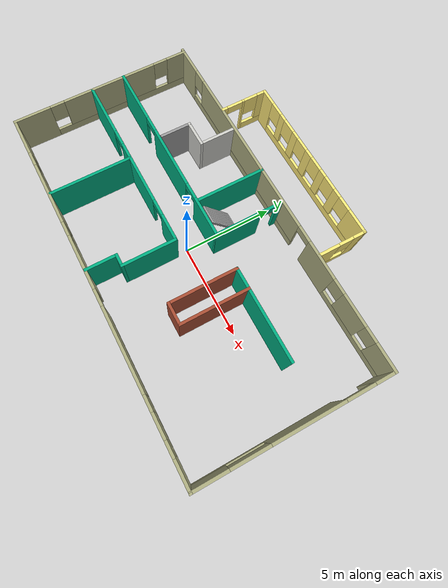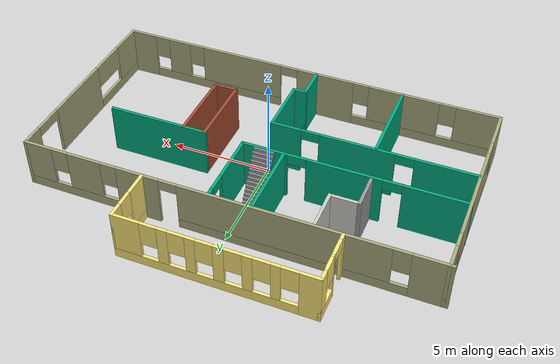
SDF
<?xml version='1.0'?>
<sdf version='1.6'>
  <model name='MyHouse'>
    <pose frame=''>0 1.26463 0 0 -0 0</pose>
    <link name='Stairs_0'>
      <visual name='Stairs_0_Visual_0'>
        <pose frame=''>-0.366202 1.61494 0.083333 0 -0 0</pose>
        <geometry>
          <box>
            <size>1 0.106176 0.166667</size>
          </box>
        </geometry>
        <material>
          <script>
            <uri>file://media/materials/scripts/gazebo.material</uri>
            <name>Gazebo/Grey</name>
          </script>
          <ambient>1 1 1 1</ambient>
        </material>
        <meta>
          <layer>0</layer>
        </meta>
      </visual>
      <collision name='Stairs_0_Collision_0'>
        <geometry>
          <box>
            <size>1 0.106176 0.166667</size>
          </box>
        </geometry>
        <pose frame=''>-0.366202 1.61494 0.083333 0 -0 0</pose>
      </collision>
      <visual name='Stairs_0_Visual_1'>
        <pose frame=''>-0.366202 1.50876 0.25 0 -0 0</pose>
        <geometry>
          <box>
            <size>1 0.106176 0.166667</size>
          </box>
        </geometry>
        <material>
          <script>
            <uri>file://media/materials/scripts/gazebo.material</uri>
            <name>Gazebo/Grey</name>
          </script>
          <ambient>1 1 1 1</ambient>
        </material>
        <meta>
          <layer>0</layer>
        </meta>
      </visual>
      <collision name='Stairs_0_Collision_1'>
        <geometry>
          <box>
            <size>1 0.106176 0.166667</size>
          </box>
        </geometry>
        <pose frame=''>-0.366202 1.50876 0.25 0 -0 0</pose>
      </collision>
      <visual name='Stairs_0_Visual_2'>
        <pose frame=''>-0.366202 1.40258 0.416667 0 -0 0</pose>
        <geometry>
          <box>
            <size>1 0.106176 0.166667</size>
          </box>
        </geometry>
        <material>
          <script>
            <uri>file://media/materials/scripts/gazebo.material</uri>
            <name>Gazebo/Grey</name>
          </script>
          <ambient>1 1 1 1</ambient>
        </material>
        <meta>
          <layer>0</layer>
        </meta>
      </visual>
      <collision name='Stairs_0_Collision_2'>
        <geometry>
          <box>
            <size>1 0.106176 0.166667</size>
          </box>
        </geometry>
        <pose frame=''>-0.366202 1.40258 0.416667 0 -0 0</pose>
      </collision>
      <visual name='Stairs_0_Visual_3'>
        <pose frame=''>-0.366202 1.29641 0.583333 0 -0 0</pose>
        <geometry>
          <box>
            <size>1 0.106176 0.166667</size>
          </box>
        </geometry>
        <material>
          <script>
            <uri>file://media/materials/scripts/gazebo.material</uri>
            <name>Gazebo/Grey</name>
          </script>
          <ambient>1 1 1 1</ambient>
        </material>
        <meta>
          <layer>0</layer>
        </meta>
      </visual>
      <collision name='Stairs_0_Collision_3'>
        <geometry>
          <box>
            <size>1 0.106176 0.166667</size>
          </box>
        </geometry>
        <pose frame=''>-0.366202 1.29641 0.583333 0 -0 0</pose>
      </collision>
      <visual name='Stairs_0_Visual_4'>
        <pose frame=''>-0.366202 1.19023 0.75 0 -0 0</pose>
        <geometry>
          <box>
            <size>1 0.106176 0.166667</size>
          </box>
        </geometry>
        <material>
          <script>
            <uri>file://media/materials/scripts/gazebo.material</uri>
            <name>Gazebo/Grey</name>
          </script>
          <ambient>1 1 1 1</ambient>
        </material>
        <meta>
          <layer>0</layer>
        </meta>
      </visual>
      <collision name='Stairs_0_Collision_4'>
        <geometry>
          <box>
            <size>1 0.106176 0.166667</size>
          </box>
        </geometry>
        <pose frame=''>-0.366202 1.19023 0.75 0 -0 0</pose>
      </collision>
      <visual name='Stairs_0_Visual_5'>
        <pose frame=''>-0.366202 1.08406 0.916667 0 -0 0</pose>
        <geometry>
          <box>
            <size>1 0.106176 0.166667</size>
          </box>
        </geometry>
        <material>
          <script>
            <uri>file://media/materials/scripts/gazebo.material</uri>
            <name>Gazebo/Grey</name>
          </script>
          <ambient>1 1 1 1</ambient>
        </material>
        <meta>
          <layer>0</layer>
        </meta>
      </visual>
      <collision name='Stairs_0_Collision_5'>
        <geometry>
          <box>
            <size>1 0.106176 0.166667</size>
          </box>
        </geometry>
        <pose frame=''>-0.366202 1.08406 0.916667 0 -0 0</pose>
      </collision>
      <visual name='Stairs_0_Visual_6'>
        <pose frame=''>-0.366202 0.977881 1.08333 0 -0 0</pose>
        <geometry>
          <box>
            <size>1 0.106176 0.166667</size>
          </box>
        </geometry>
        <material>
          <script>
            <uri>file://media/materials/scripts/gazebo.material</uri>
            <name>Gazebo/Grey</name>
          </script>
          <ambient>1 1 1 1</ambient>
        </material>
        <meta>
          <layer>0</layer>
        </meta>
      </visual>
      <collision name='Stairs_0_Collision_6'>
        <geometry>
          <box>
            <size>1 0.106176 0.166667</size>
          </box>
        </geometry>
        <pose frame=''>-0.366202 0.977881 1.08333 0 -0 0</pose>
      </collision>
      <visual name='Stairs_0_Visual_7'>
        <pose frame=''>-0.366202 0.871705 1.25 0 -0 0</pose>
        <geometry>
          <box>
            <size>1 0.106176 0.166667</size>
          </box>
        </geometry>
        <material>
          <script>
            <uri>file://media/materials/scripts/gazebo.material</uri>
            <name>Gazebo/Grey</name>
          </script>
          <ambient>1 1 1 1</ambient>
        </material>
        <meta>
          <layer>0</layer>
        </meta>
      </visual>
      <collision name='Stairs_0_Collision_7'>
        <geometry>
          <box>
            <size>1 0.106176 0.166667</size>
          </box>
        </geometry>
        <pose frame=''>-0.366202 0.871705 1.25 0 -0 0</pose>
      </collision>
      <visual name='Stairs_0_Visual_8'>
        <pose frame=''>-0.366202 0.765529 1.41667 0 -0 0</pose>
        <geometry>
          <box>
            <size>1 0.106176 0.166667</size>
          </box>
        </geometry>
        <material>
          <script>
            <uri>file://media/materials/scripts/gazebo.material</uri>
            <name>Gazebo/Grey</name>
          </script>
          <ambient>1 1 1 1</ambient>
        </material>
        <meta>
          <layer>0</layer>
        </meta>
      </visual>
      <collision name='Stairs_0_Collision_8'>
        <geometry>
          <box>
            <size>1 0.106176 0.166667</size>
          </box>
        </geometry>
        <pose frame=''>-0.366202 0.765529 1.41667 0 -0 0</pose>
      </collision>
      <visual name='Stairs_0_Visual_9'>
        <pose frame=''>-0.366202 0.659354 1.58333 0 -0 0</pose>
        <geometry>
          <box>
            <size>1 0.106176 0.166667</size>
          </box>
        </geometry>
        <material>
          <script>
            <uri>file://media/materials/scripts/gazebo.material</uri>
            <name>Gazebo/Grey</name>
          </script>
          <ambient>1 1 1 1</ambient>
        </material>
        <meta>
          <layer>0</layer>
        </meta>
      </visual>
      <collision name='Stairs_0_Collision_9'>
        <geometry>
          <box>
            <size>1 0.106176 0.166667</size>
          </box>
        </geometry>
        <pose frame=''>-0.366202 0.659354 1.58333 0 -0 0</pose>
      </collision>
      <visual name='Stairs_0_Visual_10'>
        <pose frame=''>-0.366202 0.553178 1.75 0 -0 0</pose>
        <geometry>
          <box>
            <size>1 0.106176 0.166667</size>
          </box>
        </geometry>
        <material>
          <script>
            <uri>file://media/materials/scripts/gazebo.material</uri>
            <name>Gazebo/Grey</name>
          </script>
          <ambient>1 1 1 1</ambient>
        </material>
        <meta>
          <layer>0</layer>
        </meta>
      </visual>
      <collision name='Stairs_0_Collision_10'>
        <geometry>
          <box>
            <size>1 0.106176 0.166667</size>
          </box>
        </geometry>
        <pose frame=''>-0.366202 0.553178 1.75 0 -0 0</pose>
      </collision>
      <visual name='Stairs_0_Visual_11'>
        <pose frame=''>-0.366202 0.447002 1.91667 0 -0 0</pose>
        <geometry>
          <box>
            <size>1 0.106176 0.166667</size>
          </box>
        </geometry>
        <material>
          <script>
            <uri>file://media/materials/scripts/gazebo.material</uri>
            <name>Gazebo/Grey</name>
          </script>
          <ambient>1 1 1 1</ambient>
        </material>
        <meta>
          <layer>0</layer>
        </meta>
      </visual>
      <collision name='Stairs_0_Collision_11'>
        <geometry>
          <box>
            <size>1 0.106176 0.166667</size>
          </box>
        </geometry>
        <pose frame=''>-0.366202 0.447002 1.91667 0 -0 0</pose>
      </collision>
      <visual name='Stairs_0_Visual_12'>
        <pose frame=''>-0.366202 0.340826 2.08333 0 -0 0</pose>
        <geometry>
          <box>
            <size>1 0.106176 0.166667</size>
          </box>
        </geometry>
        <material>
          <script>
            <uri>file://media/materials/scripts/gazebo.material</uri>
            <name>Gazebo/Grey</name>
          </script>
          <ambient>1 1 1 1</ambient>
        </material>
        <meta>
          <layer>0</layer>
        </meta>
      </visual>
      <collision name='Stairs_0_Collision_12'>
        <geometry>
          <box>
            <size>1 0.106176 0.166667</size>
          </box>
        </geometry>
        <pose frame=''>-0.366202 0.340826 2.08333 0 -0 0</pose>
      </collision>
      <visual name='Stairs_0_Visual_13'>
        <pose frame=''>-0.366202 0.234651 2.25 0 -0 0</pose>
        <geometry>
          <box>
            <size>1 0.106176 0.166667</size>
          </box>
        </geometry>
        <material>
          <script>
            <uri>file://media/materials/scripts/gazebo.material</uri>
            <name>Gazebo/Grey</name>
          </script>
          <ambient>1 1 1 1</ambient>
        </material>
        <meta>
          <layer>0</layer>
        </meta>
      </visual>
      <collision name='Stairs_0_Collision_13'>
        <geometry>
          <box>
            <size>1 0.106176 0.166667</size>
          </box>
        </geometry>
        <pose frame=''>-0.366202 0.234651 2.25 0 -0 0</pose>
      </collision>
      <visual name='Stairs_0_Visual_14'>
        <pose frame=''>-0.366202 0.128475 2.41667 0 -0 0</pose>
        <geometry>
          <box>
            <size>1 0.106176 0.166667</size>
          </box>
        </geometry>
        <material>
          <script>
            <uri>file://media/materials/scripts/gazebo.material</uri>
            <name>Gazebo/Grey</name>
          </script>
          <ambient>1 1 1 1</ambient>
        </material>
        <meta>
          <layer>0</layer>
        </meta>
      </visual>
      <collision name='Stairs_0_Collision_14'>
        <geometry>
          <box>
            <size>1 0.106176 0.166667</size>
          </box>
        </geometry>
        <pose frame=''>-0.366202 0.128475 2.41667 0 -0 0</pose>
      </collision>
    </link>
    <link name='Wall_16'>
      <pose frame=''>0 3.73537 0 0 -0 0</pose>
      <visual name='Wall_16_Visual_0'>
        <pose frame=''>-9.20037 0 1.25 0 -0 0</pose>
        <geometry>
          <box>
            <size>1.74927 0.15 2.5</size>
          </box>
        </geometry>
        <material>
          <script>
            <uri>file://media/materials/scripts/gazebo.material</uri>
            <name>Gazebo/Grey</name>
          </script>
          <ambient>0.666667 0.666667 0.498039 1</ambient>
        </material>
        <meta>
          <layer>0</layer>
        </meta>
      </visual>
      <collision name='Wall_16_Collision_0'>
        <geometry>
          <box>
            <size>1.74927 0.15 2.5</size>
          </box>
        </geometry>
        <pose frame=''>-9.20037 0 1.25 0 -0 0</pose>
      </collision>
      <visual name='Wall_16_Visual_1'>
        <pose frame=''>4.20315 0 1.25 0 -0 0</pose>
        <geometry>
          <box>
            <size>2.12003 0.15 2.5</size>
          </box>
        </geometry>
        <material>
          <script>
            <uri>file://media/materials/scripts/gazebo.material</uri>
            <name>Gazebo/Grey</name>
          </script>
          <ambient>0.666667 0.666667 0.498039 1</ambient>
        </material>
        <meta>
          <layer>0</layer>
        </meta>
      </visual>
      <collision name='Wall_16_Collision_1'>
        <geometry>
          <box>
            <size>2.12003 0.15 2.5</size>
          </box>
        </geometry>
        <pose frame=''>4.20315 0 1.25 0 -0 0</pose>
      </collision>
      <visual name='Wall_16_Visual_2'>
        <pose frame=''>-3.0413 0 0.25 0 -0 0</pose>
        <geometry>
          <box>
            <size>10.5689 0.15 0.5</size>
          </box>
        </geometry>
        <material>
          <script>
            <uri>file://media/materials/scripts/gazebo.material</uri>
            <name>Gazebo/Grey</name>
          </script>
          <ambient>0.666667 0.666667 0.498039 1</ambient>
        </material>
        <meta>
          <layer>0</layer>
        </meta>
      </visual>
      <collision name='Wall_16_Collision_2'>
        <geometry>
          <box>
            <size>10.5689 0.15 0.5</size>
          </box>
        </geometry>
        <pose frame=''>-3.0413 0 0.25 0 -0 0</pose>
      </collision>
      <visual name='Wall_16_Visual_3'>
        <pose frame=''>7.66908 0 0.25 0 -0 0</pose>
        <geometry>
          <box>
            <size>4.81184 0.15 0.5</size>
          </box>
        </geometry>
        <material>
          <script>
            <uri>file://media/materials/scripts/gazebo.material</uri>
            <name>Gazebo/Grey</name>
          </script>
          <ambient>0.666667 0.666667 0.498039 1</ambient>
        </material>
        <meta>
          <layer>0</layer>
        </meta>
      </visual>
      <collision name='Wall_16_Collision_3'>
        <geometry>
          <box>
            <size>4.81184 0.15 0.5</size>
          </box>
        </geometry>
        <pose frame=''>7.66908 0 0.25 0 -0 0</pose>
      </collision>
      <visual name='Wall_16_Visual_4'>
        <pose frame=''>-2.6413 0 1.5 0 -0 0</pose>
        <geometry>
          <box>
            <size>9.76886 0.15 2</size>
          </box>
        </geometry>
        <material>
          <script>
            <uri>file://media/materials/scripts/gazebo.material</uri>
            <name>Gazebo/Grey</name>
          </script>
          <ambient>0.666667 0.666667 0.498039 1</ambient>
        </material>
        <meta>
          <layer>0</layer>
        </meta>
      </visual>
      <collision name='Wall_16_Collision_4'>
        <geometry>
          <box>
            <size>9.76886 0.15 2</size>
          </box>
        </geometry>
        <pose frame=''>-2.6413 0 1.5 0 -0 0</pose>
      </collision>
      <visual name='Wall_16_Visual_5'>
        <pose frame=''>-2.6413 0 1.5 0 -0 0</pose>
        <geometry>
          <box>
            <size>9.76886 0.15 2</size>
          </box>
        </geometry>
        <material>
          <script>
            <uri>file://media/materials/scripts/gazebo.material</uri>
            <name>Gazebo/Grey</name>
          </script>
          <ambient>0.666667 0.666667 0.498039 1</ambient>
        </material>
        <meta>
          <layer>0</layer>
        </meta>
      </visual>
      <collision name='Wall_16_Collision_5'>
        <geometry>
          <box>
            <size>9.76886 0.15 2</size>
          </box>
        </geometry>
        <pose frame=''>-2.6413 0 1.5 0 -0 0</pose>
      </collision>
      <visual name='Wall_16_Visual_6'>
        <pose frame=''>6.9244 0 1.5 0 -0 0</pose>
        <geometry>
          <box>
            <size>1.72249 0.15 2</size>
          </box>
        </geometry>
        <material>
          <script>
            <uri>file://media/materials/scripts/gazebo.material</uri>
            <name>Gazebo/Grey</name>
          </script>
          <ambient>0.666667 0.666667 0.498039 1</ambient>
        </material>
        <meta>
          <layer>0</layer>
        </meta>
      </visual>
      <collision name='Wall_16_Collision_6'>
        <geometry>
          <box>
            <size>1.72249 0.15 2</size>
          </box>
        </geometry>
        <pose frame=''>6.9244 0 1.5 0 -0 0</pose>
      </collision>
      <visual name='Wall_16_Visual_7'>
        <pose frame=''>9.33032 0 1.5 0 -0 0</pose>
        <geometry>
          <box>
            <size>1.48935 0.15 2</size>
          </box>
        </geometry>
        <material>
          <script>
            <uri>file://media/materials/scripts/gazebo.material</uri>
            <name>Gazebo/Grey</name>
          </script>
          <ambient>0.666667 0.666667 0.498039 1</ambient>
        </material>
        <meta>
          <layer>0</layer>
        </meta>
      </visual>
      <collision name='Wall_16_Collision_7'>
        <geometry>
          <box>
            <size>1.48935 0.15 2</size>
          </box>
        </geometry>
        <pose frame=''>9.33032 0 1.5 0 -0 0</pose>
      </collision>
      <visual name='Wall_16_Visual_8'>
        <pose frame=''>-7.92574 0 1.9 0 -0 0</pose>
        <geometry>
          <box>
            <size>0.8 0.15 1.2</size>
          </box>
        </geometry>
        <material>
          <script>
            <uri>file://media/materials/scripts/gazebo.material</uri>
            <name>Gazebo/Grey</name>
          </script>
          <ambient>0.666667 0.666667 0.498039 1</ambient>
        </material>
        <meta>
          <layer>0</layer>
        </meta>
      </visual>
      <collision name='Wall_16_Collision_8'>
        <geometry>
          <box>
            <size>0.8 0.15 1.2</size>
          </box>
        </geometry>
        <pose frame=''>-7.92574 0 1.9 0 -0 0</pose>
      </collision>
      <visual name='Wall_16_Visual_9'>
        <pose frame=''>5.66316 0 1.9 0 -0 0</pose>
        <geometry>
          <box>
            <size>0.8 0.15 1.2</size>
          </box>
        </geometry>
        <material>
          <script>
            <uri>file://media/materials/scripts/gazebo.material</uri>
            <name>Gazebo/Grey</name>
          </script>
          <ambient>0.666667 0.666667 0.498039 1</ambient>
        </material>
        <meta>
          <layer>0</layer>
        </meta>
      </visual>
      <collision name='Wall_16_Collision_9'>
        <geometry>
          <box>
            <size>0.8 0.15 1.2</size>
          </box>
        </geometry>
        <pose frame=''>5.66316 0 1.9 0 -0 0</pose>
      </collision>
      <visual name='Wall_16_Visual_10'>
        <pose frame=''>8.18565 0 1.9 0 -0 0</pose>
        <geometry>
          <box>
            <size>0.8 0.15 1.2</size>
          </box>
        </geometry>
        <material>
          <script>
            <uri>file://media/materials/scripts/gazebo.material</uri>
            <name>Gazebo/Grey</name>
          </script>
          <ambient>0.666667 0.666667 0.498039 1</ambient>
        </material>
        <meta>
          <layer>0</layer>
        </meta>
      </visual>
      <collision name='Wall_16_Collision_10'>
        <geometry>
          <box>
            <size>0.8 0.15 1.2</size>
          </box>
        </geometry>
        <pose frame=''>8.18565 0 1.9 0 -0 0</pose>
      </collision>
      <visual name='Wall_16_Visual_11'>
        <pose frame=''>2.69313 0 2.25 0 -0 0</pose>
        <geometry>
          <box>
            <size>0.9 0.15 0.5</size>
          </box>
        </geometry>
        <material>
          <script>
            <uri>file://media/materials/scripts/gazebo.material</uri>
            <name>Gazebo/Grey</name>
          </script>
          <ambient>0.666667 0.666667 0.498039 1</ambient>
        </material>
        <meta>
          <layer>0</layer>
        </meta>
      </visual>
      <collision name='Wall_16_Collision_11'>
        <geometry>
          <box>
            <size>0.9 0.15 0.5</size>
          </box>
        </geometry>
        <pose frame=''>2.69313 0 2.25 0 -0 0</pose>
      </collision>
      <visual name='Wall_16_Visual_12'>
        <pose frame=''>2.69313 0 2.25 0 -0 0</pose>
        <geometry>
          <box>
            <size>0.9 0.15 0.5</size>
          </box>
        </geometry>
        <material>
          <script>
            <uri>file://media/materials/scripts/gazebo.material</uri>
            <name>Gazebo/Grey</name>
          </script>
          <ambient>0.666667 0.666667 0.498039 1</ambient>
        </material>
        <meta>
          <layer>0</layer>
        </meta>
      </visual>
      <collision name='Wall_16_Collision_12'>
        <geometry>
          <box>
            <size>0.9 0.15 0.5</size>
          </box>
        </geometry>
        <pose frame=''>2.69313 0 2.25 0 -0 0</pose>
      </collision>
    </link>
    <link name='Wall_27'>
      <pose frame=''>10 -1.31462 0 0 0 -1.5708</pose>
      <visual name='Wall_27_Visual_0'>
        <pose frame=''>-4.56171 0 1.25 0 -0 0</pose>
        <geometry>
          <box>
            <size>1.12659 0.15 2.5</size>
          </box>
        </geometry>
        <material>
          <script>
            <uri>file://media/materials/scripts/gazebo.material</uri>
            <name>Gazebo/Grey</name>
          </script>
          <ambient>0.666667 0.666667 0.498039 1</ambient>
        </material>
        <meta>
          <layer>0</layer>
        </meta>
      </visual>
      <collision name='Wall_27_Collision_0'>
        <geometry>
          <box>
            <size>1.12659 0.15 2.5</size>
          </box>
        </geometry>
        <pose frame=''>-4.56171 0 1.25 0 -0 0</pose>
      </collision>
      <visual name='Wall_27_Visual_1'>
        <pose frame=''>-0.627153 0 1.25 0 -0 0</pose>
        <geometry>
          <box>
            <size>3.74252 0.15 2.5</size>
          </box>
        </geometry>
        <material>
          <script>
            <uri>file://media/materials/scripts/gazebo.material</uri>
            <name>Gazebo/Grey</name>
          </script>
          <ambient>0.666667 0.666667 0.498039 1</ambient>
        </material>
        <meta>
          <layer>0</layer>
        </meta>
      </visual>
      <collision name='Wall_27_Collision_1'>
        <geometry>
          <box>
            <size>3.74252 0.15 2.5</size>
          </box>
        </geometry>
        <pose frame=''>-0.627153 0 1.25 0 -0 0</pose>
      </collision>
      <visual name='Wall_27_Visual_2'>
        <pose frame=''>3.18455 0 0.25 0 -0 0</pose>
        <geometry>
          <box>
            <size>3.8809 0.15 0.5</size>
          </box>
        </geometry>
        <material>
          <script>
            <uri>file://media/materials/scripts/gazebo.material</uri>
            <name>Gazebo/Grey</name>
          </script>
          <ambient>0.666667 0.666667 0.498039 1</ambient>
        </material>
        <meta>
          <layer>0</layer>
        </meta>
      </visual>
      <collision name='Wall_27_Collision_2'>
        <geometry>
          <box>
            <size>3.8809 0.15 0.5</size>
          </box>
        </geometry>
        <pose frame=''>3.18455 0 0.25 0 -0 0</pose>
      </collision>
      <visual name='Wall_27_Visual_3'>
        <pose frame=''>4.18455 0 1.5 0 -0 0</pose>
        <geometry>
          <box>
            <size>1.88089 0.15 2</size>
          </box>
        </geometry>
        <material>
          <script>
            <uri>file://media/materials/scripts/gazebo.material</uri>
            <name>Gazebo/Grey</name>
          </script>
          <ambient>0.666667 0.666667 0.498039 1</ambient>
        </material>
        <meta>
          <layer>0</layer>
        </meta>
      </visual>
      <collision name='Wall_27_Collision_3'>
        <geometry>
          <box>
            <size>1.88089 0.15 2</size>
          </box>
        </geometry>
        <pose frame=''>4.18455 0 1.5 0 -0 0</pose>
      </collision>
      <visual name='Wall_27_Visual_4'>
        <pose frame=''>2.2441 0 1.9 0 -0 0</pose>
        <geometry>
          <box>
            <size>2 0.15 1.2</size>
          </box>
        </geometry>
        <material>
          <script>
            <uri>file://media/materials/scripts/gazebo.material</uri>
            <name>Gazebo/Grey</name>
          </script>
          <ambient>0.666667 0.666667 0.498039 1</ambient>
        </material>
        <meta>
          <layer>0</layer>
        </meta>
      </visual>
      <collision name='Wall_27_Collision_4'>
        <geometry>
          <box>
            <size>2 0.15 1.2</size>
          </box>
        </geometry>
        <pose frame=''>2.2441 0 1.9 0 -0 0</pose>
      </collision>
      <visual name='Wall_27_Visual_5'>
        <pose frame=''>-3.24841 0 2.25 0 -0 0</pose>
        <geometry>
          <box>
            <size>1.5 0.15 0.5</size>
          </box>
        </geometry>
        <material>
          <script>
            <uri>file://media/materials/scripts/gazebo.material</uri>
            <name>Gazebo/Grey</name>
          </script>
          <ambient>0.666667 0.666667 0.498039 1</ambient>
        </material>
        <meta>
          <layer>0</layer>
        </meta>
      </visual>
      <collision name='Wall_27_Collision_5'>
        <geometry>
          <box>
            <size>1.5 0.15 0.5</size>
          </box>
        </geometry>
        <pose frame=''>-3.24841 0 2.25 0 -0 0</pose>
      </collision>
    </link>
    <link name='Wall_28'>
      <pose frame=''>0.075 -6.36463 0 0 -0 3.14159</pose>
      <visual name='Wall_28_Visual_0'>
        <pose frame=''>-9.25532 0 1.25 0 -0 0</pose>
        <geometry>
          <box>
            <size>1.48935 0.15 2.5</size>
          </box>
        </geometry>
        <material>
          <script>
            <uri>file://media/materials/scripts/gazebo.material</uri>
            <name>Gazebo/Grey</name>
          </script>
          <ambient>0.666667 0.666667 0.498039 1</ambient>
        </material>
        <meta>
          <layer>0</layer>
        </meta>
      </visual>
      <collision name='Wall_28_Collision_0'>
        <geometry>
          <box>
            <size>1.48935 0.15 2.5</size>
          </box>
        </geometry>
        <pose frame=''>-9.25532 0 1.25 0 -0 0</pose>
      </collision>
      <visual name='Wall_28_Visual_1'>
        <pose frame=''>1.08889 0 1.25 0 -0 0</pose>
        <geometry>
          <box>
            <size>3.0151 0.15 2.5</size>
          </box>
        </geometry>
        <material>
          <script>
            <uri>file://media/materials/scripts/gazebo.material</uri>
            <name>Gazebo/Grey</name>
          </script>
          <ambient>0.666667 0.666667 0.498039 1</ambient>
        </material>
        <meta>
          <layer>0</layer>
        </meta>
      </visual>
      <collision name='Wall_28_Collision_1'>
        <geometry>
          <box>
            <size>3.0151 0.15 2.5</size>
          </box>
        </geometry>
        <pose frame=''>1.08889 0 1.25 0 -0 0</pose>
      </collision>
      <visual name='Wall_28_Visual_2'>
        <pose frame=''>-4.91465 0 0.25 0 -0 0</pose>
        <geometry>
          <box>
            <size>7.19198 0.15 0.5</size>
          </box>
        </geometry>
        <material>
          <script>
            <uri>file://media/materials/scripts/gazebo.material</uri>
            <name>Gazebo/Grey</name>
          </script>
          <ambient>0.666667 0.666667 0.498039 1</ambient>
        </material>
        <meta>
          <layer>0</layer>
        </meta>
      </visual>
      <collision name='Wall_28_Collision_2'>
        <geometry>
          <box>
            <size>7.19198 0.15 0.5</size>
          </box>
        </geometry>
        <pose frame=''>-4.91465 0 0.25 0 -0 0</pose>
      </collision>
      <visual name='Wall_28_Visual_3'>
        <pose frame=''>6.29822 0 0.25 0 -0 0</pose>
        <geometry>
          <box>
            <size>7.40356 0.15 0.5</size>
          </box>
        </geometry>
        <material>
          <script>
            <uri>file://media/materials/scripts/gazebo.material</uri>
            <name>Gazebo/Grey</name>
          </script>
          <ambient>0.666667 0.666667 0.498039 1</ambient>
        </material>
        <meta>
          <layer>0</layer>
        </meta>
      </visual>
      <collision name='Wall_28_Collision_3'>
        <geometry>
          <box>
            <size>7.40356 0.15 0.5</size>
          </box>
        </geometry>
        <pose frame=''>6.29822 0 0.25 0 -0 0</pose>
      </collision>
      <visual name='Wall_28_Visual_4'>
        <pose frame=''>-7.09351 0 1.5 0 -0 0</pose>
        <geometry>
          <box>
            <size>1.23426 0.15 2</size>
          </box>
        </geometry>
        <material>
          <script>
            <uri>file://media/materials/scripts/gazebo.material</uri>
            <name>Gazebo/Grey</name>
          </script>
          <ambient>0.666667 0.666667 0.498039 1</ambient>
        </material>
        <meta>
          <layer>0</layer>
        </meta>
      </visual>
      <collision name='Wall_28_Collision_4'>
        <geometry>
          <box>
            <size>1.23426 0.15 2</size>
          </box>
        </geometry>
        <pose frame=''>-7.09351 0 1.5 0 -0 0</pose>
      </collision>
      <visual name='Wall_28_Visual_5'>
        <pose frame=''>-3.49752 0 1.5 0 -0 0</pose>
        <geometry>
          <box>
            <size>4.35772 0.15 2</size>
          </box>
        </geometry>
        <material>
          <script>
            <uri>file://media/materials/scripts/gazebo.material</uri>
            <name>Gazebo/Grey</name>
          </script>
          <ambient>0.666667 0.666667 0.498039 1</ambient>
        </material>
        <meta>
          <layer>0</layer>
        </meta>
      </visual>
      <collision name='Wall_28_Collision_5'>
        <geometry>
          <box>
            <size>4.35772 0.15 2</size>
          </box>
        </geometry>
        <pose frame=''>-3.49752 0 1.5 0 -0 0</pose>
      </collision>
      <visual name='Wall_28_Visual_6'>
        <pose frame=''>-3.49752 0 1.5 0 -0 0</pose>
        <geometry>
          <box>
            <size>4.35772 0.15 2</size>
          </box>
        </geometry>
        <material>
          <script>
            <uri>file://media/materials/scripts/gazebo.material</uri>
            <name>Gazebo/Grey</name>
          </script>
          <ambient>0.666667 0.666667 0.498039 1</ambient>
        </material>
        <meta>
          <layer>0</layer>
        </meta>
      </visual>
      <collision name='Wall_28_Collision_6'>
        <geometry>
          <box>
            <size>4.35772 0.15 2</size>
          </box>
        </geometry>
        <pose frame=''>-3.49752 0 1.5 0 -0 0</pose>
      </collision>
      <visual name='Wall_28_Visual_7'>
        <pose frame=''>5.19345 0 1.5 0 -0 0</pose>
        <geometry>
          <box>
            <size>3.59401 0.15 2</size>
          </box>
        </geometry>
        <material>
          <script>
            <uri>file://media/materials/scripts/gazebo.material</uri>
            <name>Gazebo/Grey</name>
          </script>
          <ambient>0.666667 0.666667 0.498039 1</ambient>
        </material>
        <meta>
          <layer>0</layer>
        </meta>
      </visual>
      <collision name='Wall_28_Collision_7'>
        <geometry>
          <box>
            <size>3.59401 0.15 2</size>
          </box>
        </geometry>
        <pose frame=''>5.19345 0 1.5 0 -0 0</pose>
      </collision>
      <visual name='Wall_28_Visual_8'>
        <pose frame=''>8.89523 0 1.5 0 -0 0</pose>
        <geometry>
          <box>
            <size>2.20954 0.15 2</size>
          </box>
        </geometry>
        <material>
          <script>
            <uri>file://media/materials/scripts/gazebo.material</uri>
            <name>Gazebo/Grey</name>
          </script>
          <ambient>0.666667 0.666667 0.498039 1</ambient>
        </material>
        <meta>
          <layer>0</layer>
        </meta>
      </visual>
      <collision name='Wall_28_Collision_8'>
        <geometry>
          <box>
            <size>2.20954 0.15 2</size>
          </box>
        </geometry>
        <pose frame=''>8.89523 0 1.5 0 -0 0</pose>
      </collision>
      <visual name='Wall_28_Visual_9'>
        <pose frame=''>-8.11065 0 1.9 0 -0 0</pose>
        <geometry>
          <box>
            <size>0.8 0.15 1.2</size>
          </box>
        </geometry>
        <material>
          <script>
            <uri>file://media/materials/scripts/gazebo.material</uri>
            <name>Gazebo/Grey</name>
          </script>
          <ambient>0.666667 0.666667 0.498039 1</ambient>
        </material>
        <meta>
          <layer>0</layer>
        </meta>
      </visual>
      <collision name='Wall_28_Collision_9'>
        <geometry>
          <box>
            <size>0.8 0.15 1.2</size>
          </box>
        </geometry>
        <pose frame=''>-8.11065 0 1.9 0 -0 0</pose>
      </collision>
      <visual name='Wall_28_Visual_10'>
        <pose frame=''>2.99644 0 1.9 0 -0 0</pose>
        <geometry>
          <box>
            <size>0.8 0.15 1.2</size>
          </box>
        </geometry>
        <material>
          <script>
            <uri>file://media/materials/scripts/gazebo.material</uri>
            <name>Gazebo/Grey</name>
          </script>
          <ambient>0.666667 0.666667 0.498039 1</ambient>
        </material>
        <meta>
          <layer>0</layer>
        </meta>
      </visual>
      <collision name='Wall_28_Collision_10'>
        <geometry>
          <box>
            <size>0.8 0.15 1.2</size>
          </box>
        </geometry>
        <pose frame=''>2.99644 0 1.9 0 -0 0</pose>
      </collision>
      <visual name='Wall_28_Visual_11'>
        <pose frame=''>-6.07638 0 1.9 0 -0 0</pose>
        <geometry>
          <box>
            <size>0.8 0.15 1.2</size>
          </box>
        </geometry>
        <material>
          <script>
            <uri>file://media/materials/scripts/gazebo.material</uri>
            <name>Gazebo/Grey</name>
          </script>
          <ambient>0.666667 0.666667 0.498039 1</ambient>
        </material>
        <meta>
          <layer>0</layer>
        </meta>
      </visual>
      <collision name='Wall_28_Collision_11'>
        <geometry>
          <box>
            <size>0.8 0.15 1.2</size>
          </box>
        </geometry>
        <pose frame=''>-6.07638 0 1.9 0 -0 0</pose>
      </collision>
      <visual name='Wall_28_Visual_12'>
        <pose frame=''>7.39046 0 1.9 0 -0 0</pose>
        <geometry>
          <box>
            <size>0.8 0.15 1.2</size>
          </box>
        </geometry>
        <material>
          <script>
            <uri>file://media/materials/scripts/gazebo.material</uri>
            <name>Gazebo/Grey</name>
          </script>
          <ambient>0.666667 0.666667 0.498039 1</ambient>
        </material>
        <meta>
          <layer>0</layer>
        </meta>
      </visual>
      <collision name='Wall_28_Collision_12'>
        <geometry>
          <box>
            <size>0.8 0.15 1.2</size>
          </box>
        </geometry>
        <pose frame=''>7.39046 0 1.9 0 -0 0</pose>
      </collision>
      <visual name='Wall_28_Visual_13'>
        <pose frame=''>-0.868663 0 2.25 0 -0 0</pose>
        <geometry>
          <box>
            <size>0.9 0.15 0.5</size>
          </box>
        </geometry>
        <material>
          <script>
            <uri>file://media/materials/scripts/gazebo.material</uri>
            <name>Gazebo/Grey</name>
          </script>
          <ambient>0.666667 0.666667 0.498039 1</ambient>
        </material>
        <meta>
          <layer>0</layer>
        </meta>
      </visual>
      <collision name='Wall_28_Collision_13'>
        <geometry>
          <box>
            <size>0.9 0.15 0.5</size>
          </box>
        </geometry>
        <pose frame=''>-0.868663 0 2.25 0 -0 0</pose>
      </collision>
      <visual name='Wall_28_Visual_14'>
        <pose frame=''>-0.868663 0 2.25 0 -0 0</pose>
        <geometry>
          <box>
            <size>0.9 0.15 0.5</size>
          </box>
        </geometry>
        <material>
          <script>
            <uri>file://media/materials/scripts/gazebo.material</uri>
            <name>Gazebo/Grey</name>
          </script>
          <ambient>0.666667 0.666667 0.498039 1</ambient>
        </material>
        <meta>
          <layer>0</layer>
        </meta>
      </visual>
      <collision name='Wall_28_Collision_14'>
        <geometry>
          <box>
            <size>0.9 0.15 0.5</size>
          </box>
        </geometry>
        <pose frame=''>-0.868663 0 2.25 0 -0 0</pose>
      </collision>
    </link>
    <link name='Wall_29'>
      <pose frame=''>-9.85 -1.31462 0 0 -0 1.5708</pose>
      <visual name='Wall_29_Visual_0'>
        <pose frame=''>-4.08798 0 1.25 0 -0 0</pose>
        <geometry>
          <box>
            <size>2.07404 0.15 2.5</size>
          </box>
        </geometry>
        <material>
          <script>
            <uri>file://media/materials/scripts/gazebo.material</uri>
            <name>Gazebo/Grey</name>
          </script>
          <ambient>0.666667 0.666667 0.498039 1</ambient>
        </material>
        <meta>
          <layer>0</layer>
        </meta>
      </visual>
      <collision name='Wall_29_Collision_0'>
        <geometry>
          <box>
            <size>2.07404 0.15 2.5</size>
          </box>
        </geometry>
        <pose frame=''>-4.08798 0 1.25 0 -0 0</pose>
      </collision>
      <visual name='Wall_29_Visual_1'>
        <pose frame=''>1.03702 0 0.25 0 -0 0</pose>
        <geometry>
          <box>
            <size>8.17596 0.15 0.5</size>
          </box>
        </geometry>
        <material>
          <script>
            <uri>file://media/materials/scripts/gazebo.material</uri>
            <name>Gazebo/Grey</name>
          </script>
          <ambient>0.666667 0.666667 0.498039 1</ambient>
        </material>
        <meta>
          <layer>0</layer>
        </meta>
      </visual>
      <collision name='Wall_29_Collision_1'>
        <geometry>
          <box>
            <size>8.17596 0.15 0.5</size>
          </box>
        </geometry>
        <pose frame=''>1.03702 0 0.25 0 -0 0</pose>
      </collision>
      <visual name='Wall_29_Visual_2'>
        <pose frame=''>0.441125 0 1.5 0 -0 0</pose>
        <geometry>
          <box>
            <size>5.38417 0.15 2</size>
          </box>
        </geometry>
        <material>
          <script>
            <uri>file://media/materials/scripts/gazebo.material</uri>
            <name>Gazebo/Grey</name>
          </script>
          <ambient>0.666667 0.666667 0.498039 1</ambient>
        </material>
        <meta>
          <layer>0</layer>
        </meta>
      </visual>
      <collision name='Wall_29_Collision_2'>
        <geometry>
          <box>
            <size>5.38417 0.15 2</size>
          </box>
        </geometry>
        <pose frame=''>0.441125 0 1.5 0 -0 0</pose>
      </collision>
      <visual name='Wall_29_Visual_3'>
        <pose frame=''>4.5291 0 1.5 0 -0 0</pose>
        <geometry>
          <box>
            <size>1.19179 0.15 2</size>
          </box>
        </geometry>
        <material>
          <script>
            <uri>file://media/materials/scripts/gazebo.material</uri>
            <name>Gazebo/Grey</name>
          </script>
          <ambient>0.666667 0.666667 0.498039 1</ambient>
        </material>
        <meta>
          <layer>0</layer>
        </meta>
      </visual>
      <collision name='Wall_29_Collision_3'>
        <geometry>
          <box>
            <size>1.19179 0.15 2</size>
          </box>
        </geometry>
        <pose frame=''>4.5291 0 1.5 0 -0 0</pose>
      </collision>
      <visual name='Wall_29_Visual_4'>
        <pose frame=''>-2.65096 0 1.9 0 -0 0</pose>
        <geometry>
          <box>
            <size>0.8 0.15 1.2</size>
          </box>
        </geometry>
        <material>
          <script>
            <uri>file://media/materials/scripts/gazebo.material</uri>
            <name>Gazebo/Grey</name>
          </script>
          <ambient>0.666667 0.666667 0.498039 1</ambient>
        </material>
        <meta>
          <layer>0</layer>
        </meta>
      </visual>
      <collision name='Wall_29_Collision_4'>
        <geometry>
          <box>
            <size>0.8 0.15 1.2</size>
          </box>
        </geometry>
        <pose frame=''>-2.65096 0 1.9 0 -0 0</pose>
      </collision>
      <visual name='Wall_29_Visual_5'>
        <pose frame=''>3.53321 0 1.9 0 -0 0</pose>
        <geometry>
          <box>
            <size>0.8 0.15 1.2</size>
          </box>
        </geometry>
        <material>
          <script>
            <uri>file://media/materials/scripts/gazebo.material</uri>
            <name>Gazebo/Grey</name>
          </script>
          <ambient>0.666667 0.666667 0.498039 1</ambient>
        </material>
        <meta>
          <layer>0</layer>
        </meta>
      </visual>
      <collision name='Wall_29_Collision_5'>
        <geometry>
          <box>
            <size>0.8 0.15 1.2</size>
          </box>
        </geometry>
        <pose frame=''>3.53321 0 1.9 0 -0 0</pose>
      </collision>
    </link>
    <link name='Wall_31'>
      <pose frame=''>-4.55879 -0.019108 0 0 -0 0</pose>
      <visual name='Wall_31_Visual_0'>
        <pose frame=''>-3.83317 0 1.25 0 -0 0</pose>
        <geometry>
          <box>
            <size>3.08365 0.15 2.5</size>
          </box>
        </geometry>
        <material>
          <script>
            <uri>file://media/materials/scripts/gazebo.material</uri>
            <name>Gazebo/Grey</name>
          </script>
          <ambient>0 0.666667 0.498039 1</ambient>
        </material>
        <meta>
          <layer>0</layer>
        </meta>
      </visual>
      <collision name='Wall_31_Collision_0'>
        <geometry>
          <box>
            <size>3.08365 0.15 2.5</size>
          </box>
        </geometry>
        <pose frame=''>-3.83317 0 1.25 0 -0 0</pose>
      </collision>
      <visual name='Wall_31_Visual_1'>
        <pose frame=''>0.400374 0 1.25 0 -0 0</pose>
        <geometry>
          <box>
            <size>3.58344 0.15 2.5</size>
          </box>
        </geometry>
        <material>
          <script>
            <uri>file://media/materials/scripts/gazebo.material</uri>
            <name>Gazebo/Grey</name>
          </script>
          <ambient>0 0.666667 0.498039 1</ambient>
        </material>
        <meta>
          <layer>0</layer>
        </meta>
      </visual>
      <collision name='Wall_31_Collision_1'>
        <geometry>
          <box>
            <size>3.58344 0.15 2.5</size>
          </box>
        </geometry>
        <pose frame=''>0.400374 0 1.25 0 -0 0</pose>
      </collision>
      <visual name='Wall_31_Visual_2'>
        <pose frame=''>4.23355 0 1.25 0 -0 0</pose>
        <geometry>
          <box>
            <size>2.2829 0.15 2.5</size>
          </box>
        </geometry>
        <material>
          <script>
            <uri>file://media/materials/scripts/gazebo.material</uri>
            <name>Gazebo/Grey</name>
          </script>
          <ambient>0 0.666667 0.498039 1</ambient>
        </material>
        <meta>
          <layer>0</layer>
        </meta>
      </visual>
      <collision name='Wall_31_Collision_2'>
        <geometry>
          <box>
            <size>2.2829 0.15 2.5</size>
          </box>
        </geometry>
        <pose frame=''>4.23355 0 1.25 0 -0 0</pose>
      </collision>
      <visual name='Wall_31_Visual_3'>
        <pose frame=''>-1.84135 0 2.25 0 -0 0</pose>
        <geometry>
          <box>
            <size>0.9 0.15 0.5</size>
          </box>
        </geometry>
        <material>
          <script>
            <uri>file://media/materials/scripts/gazebo.material</uri>
            <name>Gazebo/Grey</name>
          </script>
          <ambient>0 0.666667 0.498039 1</ambient>
        </material>
        <meta>
          <layer>0</layer>
        </meta>
      </visual>
      <collision name='Wall_31_Collision_3'>
        <geometry>
          <box>
            <size>0.9 0.15 0.5</size>
          </box>
        </geometry>
        <pose frame=''>-1.84135 0 2.25 0 -0 0</pose>
      </collision>
      <visual name='Wall_31_Visual_4'>
        <pose frame=''>2.64209 0 2.25 0 -0 0</pose>
        <geometry>
          <box>
            <size>0.9 0.15 0.5</size>
          </box>
        </geometry>
        <material>
          <script>
            <uri>file://media/materials/scripts/gazebo.material</uri>
            <name>Gazebo/Grey</name>
          </script>
          <ambient>0 0.666667 0.498039 1</ambient>
        </material>
        <meta>
          <layer>0</layer>
        </meta>
      </visual>
      <collision name='Wall_31_Collision_4'>
        <geometry>
          <box>
            <size>0.9 0.15 0.5</size>
          </box>
        </geometry>
        <pose frame=''>2.64209 0 2.25 0 -0 0</pose>
      </collision>
    </link>
    <link name='Wall_34'>
      <pose frame=''>-4.87226 -1.89063 0 0 -0 0</pose>
      <visual name='Wall_34_Visual_0'>
        <pose frame=''>-3.49906 0 1.25 0 -0 0</pose>
        <geometry>
          <box>
            <size>3.00188 0.15 2.5</size>
          </box>
        </geometry>
        <material>
          <script>
            <uri>file://media/materials/scripts/gazebo.material</uri>
            <name>Gazebo/Grey</name>
          </script>
          <ambient>0 0.666667 0.498039 1</ambient>
        </material>
        <meta>
          <layer>0</layer>
        </meta>
      </visual>
      <collision name='Wall_34_Collision_0'>
        <geometry>
          <box>
            <size>3.00188 0.15 2.5</size>
          </box>
        </geometry>
        <pose frame=''>-3.49906 0 1.25 0 -0 0</pose>
      </collision>
      <visual name='Wall_34_Visual_1'>
        <pose frame=''>0.730258 0 1.25 0 -0 0</pose>
        <geometry>
          <box>
            <size>3.65675 0.15 2.5</size>
          </box>
        </geometry>
        <material>
          <script>
            <uri>file://media/materials/scripts/gazebo.material</uri>
            <name>Gazebo/Grey</name>
          </script>
          <ambient>0 0.666667 0.498039 1</ambient>
        </material>
        <meta>
          <layer>0</layer>
        </meta>
      </visual>
      <collision name='Wall_34_Collision_1'>
        <geometry>
          <box>
            <size>3.65675 0.15 2.5</size>
          </box>
        </geometry>
        <pose frame=''>0.730258 0 1.25 0 -0 0</pose>
      </collision>
      <visual name='Wall_34_Visual_2'>
        <pose frame=''>4.22932 0 1.25 0 -0 0</pose>
        <geometry>
          <box>
            <size>1.54137 0.15 2.5</size>
          </box>
        </geometry>
        <material>
          <script>
            <uri>file://media/materials/scripts/gazebo.material</uri>
            <name>Gazebo/Grey</name>
          </script>
          <ambient>0 0.666667 0.498039 1</ambient>
        </material>
        <meta>
          <layer>0</layer>
        </meta>
      </visual>
      <collision name='Wall_34_Collision_2'>
        <geometry>
          <box>
            <size>1.54137 0.15 2.5</size>
          </box>
        </geometry>
        <pose frame=''>4.22932 0 1.25 0 -0 0</pose>
      </collision>
      <visual name='Wall_34_Visual_3'>
        <pose frame=''>-1.54812 0 2.25 0 -0 0</pose>
        <geometry>
          <box>
            <size>0.9 0.15 0.5</size>
          </box>
        </geometry>
        <material>
          <script>
            <uri>file://media/materials/scripts/gazebo.material</uri>
            <name>Gazebo/Grey</name>
          </script>
          <ambient>0 0.666667 0.498039 1</ambient>
        </material>
        <meta>
          <layer>0</layer>
        </meta>
      </visual>
      <collision name='Wall_34_Collision_3'>
        <geometry>
          <box>
            <size>0.9 0.15 0.5</size>
          </box>
        </geometry>
        <pose frame=''>-1.54812 0 2.25 0 -0 0</pose>
      </collision>
      <visual name='Wall_34_Visual_4'>
        <pose frame=''>3.00863 0 2.25 0 -0 0</pose>
        <geometry>
          <box>
            <size>0.9 0.15 0.5</size>
          </box>
        </geometry>
        <material>
          <script>
            <uri>file://media/materials/scripts/gazebo.material</uri>
            <name>Gazebo/Grey</name>
          </script>
          <ambient>0 0.666667 0.498039 1</ambient>
        </material>
        <meta>
          <layer>0</layer>
        </meta>
      </visual>
      <collision name='Wall_34_Collision_4'>
        <geometry>
          <box>
            <size>0.9 0.15 0.5</size>
          </box>
        </geometry>
        <pose frame=''>3.00863 0 2.25 0 -0 0</pose>
      </collision>
    </link>
    <link name='Wall_35'>
      <collision name='Wall_35_Collision'>
        <geometry>
          <box>
            <size>3 0.15 2.5</size>
          </box>
        </geometry>
        <pose frame=''>0 0 1.25 0 -0 0</pose>
      </collision>
      <visual name='Wall_35_Visual'>
        <pose frame=''>0 0 1.25 0 -0 0</pose>
        <geometry>
          <box>
            <size>3 0.15 2.5</size>
          </box>
        </geometry>
        <material>
          <script>
            <uri>file://media/materials/scripts/gazebo.material</uri>
            <name>Gazebo/Grey</name>
          </script>
          <ambient>0 0.666667 0.498039 1</ambient>
        </material>
        <meta>
          <layer>0</layer>
        </meta>
      </visual>
      <pose frame=''>0.052741 -3.31563 0 0 0 -1.5708</pose>
    </link>
    <link name='Wall_36'>
      <collision name='Wall_36_Collision'>
        <geometry>
          <box>
            <size>0.75 0.15 2.5</size>
          </box>
        </geometry>
        <pose frame=''>0 0 1.25 0 -0 0</pose>
      </collision>
      <visual name='Wall_36_Visual'>
        <pose frame=''>0 0 1.25 0 -0 0</pose>
        <geometry>
          <box>
            <size>0.75 0.15 2.5</size>
          </box>
        </geometry>
        <material>
          <script>
            <uri>file://media/materials/scripts/gazebo.material</uri>
            <name>Gazebo/Grey</name>
          </script>
          <ambient>0 0.666667 0.498039 1</ambient>
        </material>
        <meta>
          <layer>0</layer>
        </meta>
      </visual>
      <pose frame=''>-0.247259 -4.74063 0 0 -0 3.14159</pose>
    </link>
    <link name='Wall_37'>
      <collision name='Wall_37_Collision'>
        <geometry>
          <box>
            <size>1.75 0.15 2.5</size>
          </box>
        </geometry>
        <pose frame=''>0 0 1.25 0 -0 0</pose>
      </collision>
      <visual name='Wall_37_Visual'>
        <pose frame=''>0 0 1.25 0 -0 0</pose>
        <geometry>
          <box>
            <size>1.75 0.15 2.5</size>
          </box>
        </geometry>
        <material>
          <script>
            <uri>file://media/materials/scripts/gazebo.material</uri>
            <name>Gazebo/Grey</name>
          </script>
          <ambient>0 0.666667 0.498039 1</ambient>
        </material>
        <meta>
          <layer>0</layer>
        </meta>
      </visual>
      <pose frame=''>-0.547259 -5.54063 0 0 0 -1.5708</pose>
    </link>
    <link name='Wall_39'>
      <collision name='Wall_39_Collision'>
        <geometry>
          <box>
            <size>4.5 0.15 2.5</size>
          </box>
        </geometry>
        <pose frame=''>0 0 1.25 0 -0 0</pose>
      </collision>
      <visual name='Wall_39_Visual'>
        <pose frame=''>0 0 1.25 0 -0 0</pose>
        <geometry>
          <box>
            <size>4.5 0.15 2.5</size>
          </box>
        </geometry>
        <material>
          <script>
            <uri>file://media/materials/scripts/gazebo.material</uri>
            <name>Gazebo/Grey</name>
          </script>
          <ambient>0 0.666667 0.498039 1</ambient>
        </material>
        <meta>
          <layer>0</layer>
        </meta>
      </visual>
      <pose frame=''>-5.03708 -4.10632 0 0 0 -1.5708</pose>
    </link>
    <link name='Wall_41'>
      <collision name='Wall_41_Collision'>
        <geometry>
          <box>
            <size>5 0.15 2.5</size>
          </box>
        </geometry>
        <pose frame=''>0 0 1.25 0 -0 0</pose>
      </collision>
      <visual name='Wall_41_Visual'>
        <pose frame=''>0 0 1.25 0 -0 0</pose>
        <geometry>
          <box>
            <size>5 0.15 2.5</size>
          </box>
        </geometry>
        <material>
          <script>
            <uri>file://media/materials/scripts/gazebo.material</uri>
            <name>Gazebo/Grey</name>
          </script>
          <ambient>0 0.666667 0.498039 1</ambient>
        </material>
        <meta>
          <layer>0</layer>
        </meta>
      </visual>
      <pose frame=''>5.11813 -0.019108 0 0 -0 0</pose>
    </link>
    <link name='Wall_43'>
      <collision name='Wall_43_Collision'>
        <geometry>
          <box>
            <size>3.75 0.15 2.5</size>
          </box>
        </geometry>
        <pose frame=''>0 0 1.25 0 -0 0</pose>
      </collision>
      <visual name='Wall_43_Visual'>
        <pose frame=''>0 0 1.25 0 -0 0</pose>
        <geometry>
          <box>
            <size>3.75 0.15 2.5</size>
          </box>
        </geometry>
        <material>
          <script>
            <uri>file://media/materials/scripts/gazebo.material</uri>
            <name>Gazebo/Bricks</name>
          </script>
          <ambient>1 1 1 1</ambient>
        </material>
        <meta>
          <layer>0</layer>
        </meta>
      </visual>
      <pose frame=''>2.69313 -1.81911 0 0 0 -1.5708</pose>
    </link>
    <link name='Wall_44'>
      <collision name='Wall_44_Collision'>
        <geometry>
          <box>
            <size>1.25 0.15 2.5</size>
          </box>
        </geometry>
        <pose frame=''>0 0 1.25 0 -0 0</pose>
      </collision>
      <visual name='Wall_44_Visual'>
        <pose frame=''>0 0 1.25 0 -0 0</pose>
        <geometry>
          <box>
            <size>1.25 0.15 2.5</size>
          </box>
        </geometry>
        <material>
          <script>
            <uri>file://media/materials/scripts/gazebo.material</uri>
            <name>Gazebo/Bricks</name>
          </script>
          <ambient>1 1 1 1</ambient>
        </material>
        <meta>
          <layer>0</layer>
        </meta>
      </visual>
      <pose frame=''>3.24313 -3.61911 0 0 -0 0</pose>
    </link>
    <link name='Wall_45'>
      <collision name='Wall_45_Collision'>
        <geometry>
          <box>
            <size>3.75 0.15 2.5</size>
          </box>
        </geometry>
        <pose frame=''>0 0 1.25 0 -0 0</pose>
      </collision>
      <visual name='Wall_45_Visual'>
        <pose frame=''>0 0 1.25 0 -0 0</pose>
        <geometry>
          <box>
            <size>3.75 0.15 2.5</size>
          </box>
        </geometry>
        <material>
          <script>
            <uri>file://media/materials/scripts/gazebo.material</uri>
            <name>Gazebo/Bricks</name>
          </script>
          <ambient>1 1 1 1</ambient>
        </material>
        <meta>
          <layer>0</layer>
        </meta>
      </visual>
      <pose frame=''>3.79313 -1.81911 0 0 -0 1.5708</pose>
    </link>
    <link name='Wall_47'>
      <collision name='Wall_47_Collision'>
        <geometry>
          <box>
            <size>2 0.15 2.5</size>
          </box>
        </geometry>
        <pose frame=''>0 0 1.25 0 -0 0</pose>
      </collision>
      <visual name='Wall_47_Visual'>
        <pose frame=''>0 0 1.25 0 -0 0</pose>
        <geometry>
          <box>
            <size>2 0.15 2.5</size>
          </box>
        </geometry>
        <material>
          <script>
            <uri>file://media/materials/scripts/gazebo.material</uri>
            <name>Gazebo/CeilingTiled</name>
          </script>
          <ambient>0 0 0 1</ambient>
        </material>
        <meta>
          <layer>0</layer>
        </meta>
      </visual>
      <pose frame=''>-4.10132 2.67688 0 0 0 -1.5708</pose>
    </link>
    <link name='Wall_48'>
      <collision name='Wall_48_Collision'>
        <geometry>
          <box>
            <size>1.5 0.15 2.5</size>
          </box>
        </geometry>
        <pose frame=''>0 0 1.25 0 -0 0</pose>
      </collision>
      <visual name='Wall_48_Visual'>
        <pose frame=''>0 0 1.25 0 -0 0</pose>
        <geometry>
          <box>
            <size>1.5 0.15 2.5</size>
          </box>
        </geometry>
        <material>
          <script>
            <uri>file://media/materials/scripts/gazebo.material</uri>
            <name>Gazebo/CeilingTiled</name>
          </script>
          <ambient>0 0 0 1</ambient>
        </material>
        <meta>
          <layer>0</layer>
        </meta>
      </visual>
      <pose frame=''>-4.77632 1.75188 0 0 -0 3.14159</pose>
    </link>
    <link name='Wall_49'>
      <collision name='Wall_49_Collision'>
        <geometry>
          <box>
            <size>1.75 0.15 2.5</size>
          </box>
        </geometry>
        <pose frame=''>0 0 1.25 0 -0 0</pose>
      </collision>
      <visual name='Wall_49_Visual'>
        <pose frame=''>0 0 1.25 0 -0 0</pose>
        <geometry>
          <box>
            <size>1.75 0.15 2.5</size>
          </box>
        </geometry>
        <material>
          <script>
            <uri>file://media/materials/scripts/gazebo.material</uri>
            <name>Gazebo/Grey</name>
          </script>
          <ambient>0 0 0 1</ambient>
        </material>
        <meta>
          <layer>0</layer>
        </meta>
      </visual>
      <pose frame=''>-5.45132 0.951884 0 0 0 -1.5708</pose>
    </link>
    <link name='Wall_51'>
      <pose frame=''>-5.40325 5.06463 0 0 -0 1.5708</pose>
      <visual name='Wall_51_Visual_0'>
        <pose frame=''>-1.19633 0 1.25 0 -0 0</pose>
        <geometry>
          <box>
            <size>0.357335 0.15 2.5</size>
          </box>
        </geometry>
        <material>
          <script>
            <uri>file://media/materials/scripts/gazebo.material</uri>
            <name>Gazebo/Grey</name>
          </script>
          <ambient>1 0.913725 0.470588 1</ambient>
        </material>
        <meta>
          <layer>0</layer>
        </meta>
      </visual>
      <collision name='Wall_51_Collision_0'>
        <geometry>
          <box>
            <size>0.357335 0.15 2.5</size>
          </box>
        </geometry>
        <pose frame=''>-1.19633 0 1.25 0 -0 0</pose>
      </collision>
      <visual name='Wall_51_Visual_1'>
        <pose frame=''>-0.054441 0 1.25 0 -0 0</pose>
        <geometry>
          <box>
            <size>0.126448 0.15 2.5</size>
          </box>
        </geometry>
        <material>
          <script>
            <uri>file://media/materials/scripts/gazebo.material</uri>
            <name>Gazebo/Grey</name>
          </script>
          <ambient>1 0.913725 0.470588 1</ambient>
        </material>
        <meta>
          <layer>0</layer>
        </meta>
      </visual>
      <collision name='Wall_51_Collision_1'>
        <geometry>
          <box>
            <size>0.126448 0.15 2.5</size>
          </box>
        </geometry>
        <pose frame=''>-0.054441 0 1.25 0 -0 0</pose>
      </collision>
      <visual name='Wall_51_Visual_2'>
        <pose frame=''>0.691891 0 0.25 0 -0 0</pose>
        <geometry>
          <box>
            <size>1.36622 0.15 0.5</size>
          </box>
        </geometry>
        <material>
          <script>
            <uri>file://media/materials/scripts/gazebo.material</uri>
            <name>Gazebo/Grey</name>
          </script>
          <ambient>1 0.913725 0.470588 1</ambient>
        </material>
        <meta>
          <layer>0</layer>
        </meta>
      </visual>
      <collision name='Wall_51_Collision_2'>
        <geometry>
          <box>
            <size>1.36622 0.15 0.5</size>
          </box>
        </geometry>
        <pose frame=''>0.691891 0 0.25 0 -0 0</pose>
      </collision>
      <visual name='Wall_51_Visual_3'>
        <pose frame=''>1.09189 0 1.5 0 -0 0</pose>
        <geometry>
          <box>
            <size>0.566217 0.15 2</size>
          </box>
        </geometry>
        <material>
          <script>
            <uri>file://media/materials/scripts/gazebo.material</uri>
            <name>Gazebo/Grey</name>
          </script>
          <ambient>1 0.913725 0.470588 1</ambient>
        </material>
        <meta>
          <layer>0</layer>
        </meta>
      </visual>
      <collision name='Wall_51_Collision_3'>
        <geometry>
          <box>
            <size>0.566217 0.15 2</size>
          </box>
        </geometry>
        <pose frame=''>1.09189 0 1.5 0 -0 0</pose>
      </collision>
      <visual name='Wall_51_Visual_4'>
        <pose frame=''>0.408783 0 1.9 0 -0 0</pose>
        <geometry>
          <box>
            <size>0.8 0.15 1.2</size>
          </box>
        </geometry>
        <material>
          <script>
            <uri>file://media/materials/scripts/gazebo.material</uri>
            <name>Gazebo/Grey</name>
          </script>
          <ambient>1 0.913725 0.470588 1</ambient>
        </material>
        <meta>
          <layer>0</layer>
        </meta>
      </visual>
      <collision name='Wall_51_Collision_4'>
        <geometry>
          <box>
            <size>0.8 0.15 1.2</size>
          </box>
        </geometry>
        <pose frame=''>0.408783 0 1.9 0 -0 0</pose>
      </collision>
      <visual name='Wall_51_Visual_5'>
        <pose frame=''>-0.567665 0 2.25 0 -0 0</pose>
        <geometry>
          <box>
            <size>0.9 0.15 0.5</size>
          </box>
        </geometry>
        <material>
          <script>
            <uri>file://media/materials/scripts/gazebo.material</uri>
            <name>Gazebo/Grey</name>
          </script>
          <ambient>1 0.913725 0.470588 1</ambient>
        </material>
        <meta>
          <layer>0</layer>
        </meta>
      </visual>
      <collision name='Wall_51_Collision_5'>
        <geometry>
          <box>
            <size>0.9 0.15 0.5</size>
          </box>
        </geometry>
        <pose frame=''>-0.567665 0 2.25 0 -0 0</pose>
      </collision>
    </link>
    <link name='Wall_52'>
      <pose frame=''>-0.728246 6.36463 0 0 -0 0</pose>
      <visual name='Wall_52_Visual_0'>
        <pose frame=''>-4.26154 0 1.25 0 -0 0</pose>
        <geometry>
          <box>
            <size>0.97693 0.15 2.5</size>
          </box>
        </geometry>
        <material>
          <script>
            <uri>file://media/materials/scripts/gazebo.material</uri>
            <name>Gazebo/Grey</name>
          </script>
          <ambient>1 0.913725 0.470588 1</ambient>
        </material>
        <meta>
          <layer>0</layer>
        </meta>
      </visual>
      <collision name='Wall_52_Collision_0'>
        <geometry>
          <box>
            <size>0.97693 0.15 2.5</size>
          </box>
        </geometry>
        <pose frame=''>-4.26154 0 1.25 0 -0 0</pose>
      </collision>
      <visual name='Wall_52_Visual_1'>
        <pose frame=''>0.488465 0 0.25 0 -0 0</pose>
        <geometry>
          <box>
            <size>8.52307 0.15 0.5</size>
          </box>
        </geometry>
        <material>
          <script>
            <uri>file://media/materials/scripts/gazebo.material</uri>
            <name>Gazebo/Grey</name>
          </script>
          <ambient>1 0.913725 0.470588 1</ambient>
        </material>
        <meta>
          <layer>0</layer>
        </meta>
      </visual>
      <collision name='Wall_52_Collision_1'>
        <geometry>
          <box>
            <size>8.52307 0.15 0.5</size>
          </box>
        </geometry>
        <pose frame=''>0.488465 0 0.25 0 -0 0</pose>
      </collision>
      <visual name='Wall_52_Visual_2'>
        <pose frame=''>-2.76279 0 1.5 0 -0 0</pose>
        <geometry>
          <box>
            <size>0.420559 0.15 2</size>
          </box>
        </geometry>
        <material>
          <script>
            <uri>file://media/materials/scripts/gazebo.material</uri>
            <name>Gazebo/Grey</name>
          </script>
          <ambient>1 0.913725 0.470588 1</ambient>
        </material>
        <meta>
          <layer>0</layer>
        </meta>
      </visual>
      <collision name='Wall_52_Collision_2'>
        <geometry>
          <box>
            <size>0.420559 0.15 2</size>
          </box>
        </geometry>
        <pose frame=''>-2.76279 0 1.5 0 -0 0</pose>
      </collision>
      <visual name='Wall_52_Visual_3'>
        <pose frame=''>-1.52189 0 1.5 0 -0 0</pose>
        <geometry>
          <box>
            <size>0.461245 0.15 2</size>
          </box>
        </geometry>
        <material>
          <script>
            <uri>file://media/materials/scripts/gazebo.material</uri>
            <name>Gazebo/Grey</name>
          </script>
          <ambient>1 0.913725 0.470588 1</ambient>
        </material>
        <meta>
          <layer>0</layer>
        </meta>
      </visual>
      <collision name='Wall_52_Collision_3'>
        <geometry>
          <box>
            <size>0.461245 0.15 2</size>
          </box>
        </geometry>
        <pose frame=''>-1.52189 0 1.5 0 -0 0</pose>
      </collision>
      <visual name='Wall_52_Visual_4'>
        <pose frame=''>-0.240301 0 1.5 0 -0 0</pose>
        <geometry>
          <box>
            <size>0.50193 0.15 2</size>
          </box>
        </geometry>
        <material>
          <script>
            <uri>file://media/materials/scripts/gazebo.material</uri>
            <name>Gazebo/Grey</name>
          </script>
          <ambient>1 0.913725 0.470588 1</ambient>
        </material>
        <meta>
          <layer>0</layer>
        </meta>
      </visual>
      <collision name='Wall_52_Collision_4'>
        <geometry>
          <box>
            <size>0.50193 0.15 2</size>
          </box>
        </geometry>
        <pose frame=''>-0.240301 0 1.5 0 -0 0</pose>
      </collision>
      <visual name='Wall_52_Visual_5'>
        <pose frame=''>1.04129 0 1.5 0 -0 0</pose>
        <geometry>
          <box>
            <size>0.461245 0.15 2</size>
          </box>
        </geometry>
        <material>
          <script>
            <uri>file://media/materials/scripts/gazebo.material</uri>
            <name>Gazebo/Grey</name>
          </script>
          <ambient>1 0.913725 0.470588 1</ambient>
        </material>
        <meta>
          <layer>0</layer>
        </meta>
      </visual>
      <collision name='Wall_52_Collision_5'>
        <geometry>
          <box>
            <size>0.461245 0.15 2</size>
          </box>
        </geometry>
        <pose frame=''>1.04129 0 1.5 0 -0 0</pose>
      </collision>
      <visual name='Wall_52_Visual_6'>
        <pose frame=''>2.32287 0 1.5 0 -0 0</pose>
        <geometry>
          <box>
            <size>0.50193 0.15 2</size>
          </box>
        </geometry>
        <material>
          <script>
            <uri>file://media/materials/scripts/gazebo.material</uri>
            <name>Gazebo/Grey</name>
          </script>
          <ambient>1 0.913725 0.470588 1</ambient>
        </material>
        <meta>
          <layer>0</layer>
        </meta>
      </visual>
      <collision name='Wall_52_Collision_6'>
        <geometry>
          <box>
            <size>0.50193 0.15 2</size>
          </box>
        </geometry>
        <pose frame=''>2.32287 0 1.5 0 -0 0</pose>
      </collision>
      <visual name='Wall_52_Visual_7'>
        <pose frame=''>4.06192 0 1.5 0 -0 0</pose>
        <geometry>
          <box>
            <size>1.37616 0.15 2</size>
          </box>
        </geometry>
        <material>
          <script>
            <uri>file://media/materials/scripts/gazebo.material</uri>
            <name>Gazebo/Grey</name>
          </script>
          <ambient>1 0.913725 0.470588 1</ambient>
        </material>
        <meta>
          <layer>0</layer>
        </meta>
      </visual>
      <collision name='Wall_52_Collision_7'>
        <geometry>
          <box>
            <size>1.37616 0.15 2</size>
          </box>
        </geometry>
        <pose frame=''>4.06192 0 1.5 0 -0 0</pose>
      </collision>
      <visual name='Wall_52_Visual_8'>
        <pose frame=''>-3.37307 0 1.9 0 -0 0</pose>
        <geometry>
          <box>
            <size>0.8 0.15 1.2</size>
          </box>
        </geometry>
        <material>
          <script>
            <uri>file://media/materials/scripts/gazebo.material</uri>
            <name>Gazebo/Grey</name>
          </script>
          <ambient>1 0.913725 0.470588 1</ambient>
        </material>
        <meta>
          <layer>0</layer>
        </meta>
      </visual>
      <collision name='Wall_52_Collision_8'>
        <geometry>
          <box>
            <size>0.8 0.15 1.2</size>
          </box>
        </geometry>
        <pose frame=''>-3.37307 0 1.9 0 -0 0</pose>
      </collision>
      <visual name='Wall_52_Visual_9'>
        <pose frame=''>-2.15251 0 1.9 0 -0 0</pose>
        <geometry>
          <box>
            <size>0.8 0.15 1.2</size>
          </box>
        </geometry>
        <material>
          <script>
            <uri>file://media/materials/scripts/gazebo.material</uri>
            <name>Gazebo/Grey</name>
          </script>
          <ambient>1 0.913725 0.470588 1</ambient>
        </material>
        <meta>
          <layer>0</layer>
        </meta>
      </visual>
      <collision name='Wall_52_Collision_9'>
        <geometry>
          <box>
            <size>0.8 0.15 1.2</size>
          </box>
        </geometry>
        <pose frame=''>-2.15251 0 1.9 0 -0 0</pose>
      </collision>
      <visual name='Wall_52_Visual_10'>
        <pose frame=''>-0.891266 0 1.9 0 -0 0</pose>
        <geometry>
          <box>
            <size>0.8 0.15 1.2</size>
          </box>
        </geometry>
        <material>
          <script>
            <uri>file://media/materials/scripts/gazebo.material</uri>
            <name>Gazebo/Grey</name>
          </script>
          <ambient>1 0.913725 0.470588 1</ambient>
        </material>
        <meta>
          <layer>0</layer>
        </meta>
      </visual>
      <collision name='Wall_52_Collision_10'>
        <geometry>
          <box>
            <size>0.8 0.15 1.2</size>
          </box>
        </geometry>
        <pose frame=''>-0.891266 0 1.9 0 -0 0</pose>
      </collision>
      <visual name='Wall_52_Visual_11'>
        <pose frame=''>0.410664 0 1.9 0 -0 0</pose>
        <geometry>
          <box>
            <size>0.8 0.15 1.2</size>
          </box>
        </geometry>
        <material>
          <script>
            <uri>file://media/materials/scripts/gazebo.material</uri>
            <name>Gazebo/Grey</name>
          </script>
          <ambient>1 0.913725 0.470588 1</ambient>
        </material>
        <meta>
          <layer>0</layer>
        </meta>
      </visual>
      <collision name='Wall_52_Collision_11'>
        <geometry>
          <box>
            <size>0.8 0.15 1.2</size>
          </box>
        </geometry>
        <pose frame=''>0.410664 0 1.9 0 -0 0</pose>
      </collision>
      <visual name='Wall_52_Visual_12'>
        <pose frame=''>1.67191 0 1.9 0 -0 0</pose>
        <geometry>
          <box>
            <size>0.8 0.15 1.2</size>
          </box>
        </geometry>
        <material>
          <script>
            <uri>file://media/materials/scripts/gazebo.material</uri>
            <name>Gazebo/Grey</name>
          </script>
          <ambient>1 0.913725 0.470588 1</ambient>
        </material>
        <meta>
          <layer>0</layer>
        </meta>
      </visual>
      <collision name='Wall_52_Collision_12'>
        <geometry>
          <box>
            <size>0.8 0.15 1.2</size>
          </box>
        </geometry>
        <pose frame=''>1.67191 0 1.9 0 -0 0</pose>
      </collision>
      <visual name='Wall_52_Visual_13'>
        <pose frame=''>2.97384 0 1.9 0 -0 0</pose>
        <geometry>
          <box>
            <size>0.8 0.15 1.2</size>
          </box>
        </geometry>
        <material>
          <script>
            <uri>file://media/materials/scripts/gazebo.material</uri>
            <name>Gazebo/Grey</name>
          </script>
          <ambient>1 0.913725 0.470588 1</ambient>
        </material>
        <meta>
          <layer>0</layer>
        </meta>
      </visual>
      <collision name='Wall_52_Collision_13'>
        <geometry>
          <box>
            <size>0.8 0.15 1.2</size>
          </box>
        </geometry>
        <pose frame=''>2.97384 0 1.9 0 -0 0</pose>
      </collision>
    </link>
    <link name='Wall_53'>
      <pose frame=''>3.94675 5.06463 0 0 0 -1.5708</pose>
      <visual name='Wall_53_Visual_0'>
        <pose frame=''>-1.01052 0 1.25 0 -0 0</pose>
        <geometry>
          <box>
            <size>0.728958 0.15 2.5</size>
          </box>
        </geometry>
        <material>
          <script>
            <uri>file://media/materials/scripts/gazebo.material</uri>
            <name>Gazebo/Grey</name>
          </script>
          <ambient>1 0.913725 0.470588 1</ambient>
        </material>
        <meta>
          <layer>0</layer>
        </meta>
      </visual>
      <collision name='Wall_53_Collision_0'>
        <geometry>
          <box>
            <size>0.728958 0.15 2.5</size>
          </box>
        </geometry>
        <pose frame=''>-1.01052 0 1.25 0 -0 0</pose>
      </collision>
      <visual name='Wall_53_Visual_1'>
        <pose frame=''>0.364479 0 0.25 0 -0 0</pose>
        <geometry>
          <box>
            <size>2.02104 0.15 0.5</size>
          </box>
        </geometry>
        <material>
          <script>
            <uri>file://media/materials/scripts/gazebo.material</uri>
            <name>Gazebo/Grey</name>
          </script>
          <ambient>1 0.913725 0.470588 1</ambient>
        </material>
        <meta>
          <layer>0</layer>
        </meta>
      </visual>
      <collision name='Wall_53_Collision_1'>
        <geometry>
          <box>
            <size>2.02104 0.15 0.5</size>
          </box>
        </geometry>
        <pose frame=''>0.364479 0 0.25 0 -0 0</pose>
      </collision>
      <visual name='Wall_53_Visual_2'>
        <pose frame=''>0.764479 0 1.5 0 -0 0</pose>
        <geometry>
          <box>
            <size>1.22104 0.15 2</size>
          </box>
        </geometry>
        <material>
          <script>
            <uri>file://media/materials/scripts/gazebo.material</uri>
            <name>Gazebo/Grey</name>
          </script>
          <ambient>1 0.913725 0.470588 1</ambient>
        </material>
        <meta>
          <layer>0</layer>
        </meta>
      </visual>
      <collision name='Wall_53_Collision_2'>
        <geometry>
          <box>
            <size>1.22104 0.15 2</size>
          </box>
        </geometry>
        <pose frame=''>0.764479 0 1.5 0 -0 0</pose>
      </collision>
      <visual name='Wall_53_Visual_3'>
        <pose frame=''>-0.246042 0 1.9 0 -0 0</pose>
        <geometry>
          <box>
            <size>0.8 0.15 1.2</size>
          </box>
        </geometry>
        <material>
          <script>
            <uri>file://media/materials/scripts/gazebo.material</uri>
            <name>Gazebo/Grey</name>
          </script>
          <ambient>1 0.913725 0.470588 1</ambient>
        </material>
        <meta>
          <layer>0</layer>
        </meta>
      </visual>
      <collision name='Wall_53_Collision_3'>
        <geometry>
          <box>
            <size>0.8 0.15 1.2</size>
          </box>
        </geometry>
        <pose frame=''>-0.246042 0 1.9 0 -0 0</pose>
      </collision>
    </link>
    <link name='Wall_77'>
      <pose frame=''>0.741213 1.78089 0 0 -0 1.5708</pose>
      <visual name='Wall_77_Visual_0'>
        <pose frame=''>-0.601883 0 1.25 0 -0 0</pose>
        <geometry>
          <box>
            <size>2.54623 0.15 2.5</size>
          </box>
        </geometry>
        <material>
          <script>
            <uri>file://media/materials/scripts/gazebo.material</uri>
            <name>Gazebo/Grey</name>
          </script>
          <ambient>0 0.666667 0.498039 1</ambient>
        </material>
        <meta>
          <layer>0</layer>
        </meta>
      </visual>
      <collision name='Wall_77_Collision_0'>
        <geometry>
          <box>
            <size>2.54623 0.15 2.5</size>
          </box>
        </geometry>
        <pose frame=''>-0.601883 0 1.25 0 -0 0</pose>
      </collision>
      <visual name='Wall_77_Visual_1'>
        <pose frame=''>1.72312 0 1.25 0 -0 0</pose>
        <geometry>
          <box>
            <size>0.303767 0.15 2.5</size>
          </box>
        </geometry>
        <material>
          <script>
            <uri>file://media/materials/scripts/gazebo.material</uri>
            <name>Gazebo/Grey</name>
          </script>
          <ambient>0 0.666667 0.498039 1</ambient>
        </material>
        <meta>
          <layer>0</layer>
        </meta>
      </visual>
      <collision name='Wall_77_Collision_1'>
        <geometry>
          <box>
            <size>0.303767 0.15 2.5</size>
          </box>
        </geometry>
        <pose frame=''>1.72312 0 1.25 0 -0 0</pose>
      </collision>
      <visual name='Wall_77_Visual_2'>
        <pose frame=''>1.12123 0 2.25 0 -0 0</pose>
        <geometry>
          <box>
            <size>0.9 0.15 0.5</size>
          </box>
        </geometry>
        <material>
          <script>
            <uri>file://media/materials/scripts/gazebo.material</uri>
            <name>Gazebo/Grey</name>
          </script>
          <ambient>0 0.666667 0.498039 1</ambient>
        </material>
        <meta>
          <layer>0</layer>
        </meta>
      </visual>
      <collision name='Wall_77_Collision_2'>
        <geometry>
          <box>
            <size>0.9 0.15 0.5</size>
          </box>
        </geometry>
        <pose frame=''>1.12123 0 2.25 0 -0 0</pose>
      </collision>
    </link>
    <link name='Wall_79'>
      <collision name='Wall_79_Collision'>
        <geometry>
          <box>
            <size>3.75 0.15 2.5</size>
          </box>
        </geometry>
        <pose frame=''>0 0 1.25 0 -0 0</pose>
      </collision>
      <visual name='Wall_79_Visual'>
        <pose frame=''>0 0 1.25 0 -0 0</pose>
        <geometry>
          <box>
            <size>3.75 0.15 2.5</size>
          </box>
        </geometry>
        <material>
          <script>
            <uri>file://media/materials/scripts/gazebo.material</uri>
            <name>Gazebo/Grey</name>
          </script>
          <ambient>0 0.666667 0.498039 1</ambient>
        </material>
        <meta>
          <layer>0</layer>
        </meta>
      </visual>
      <pose frame=''>-1.28912 1.90199 0 0 0 -1.5708</pose>
    </link>
    <static>1</static>
  </model>
</sdf>
